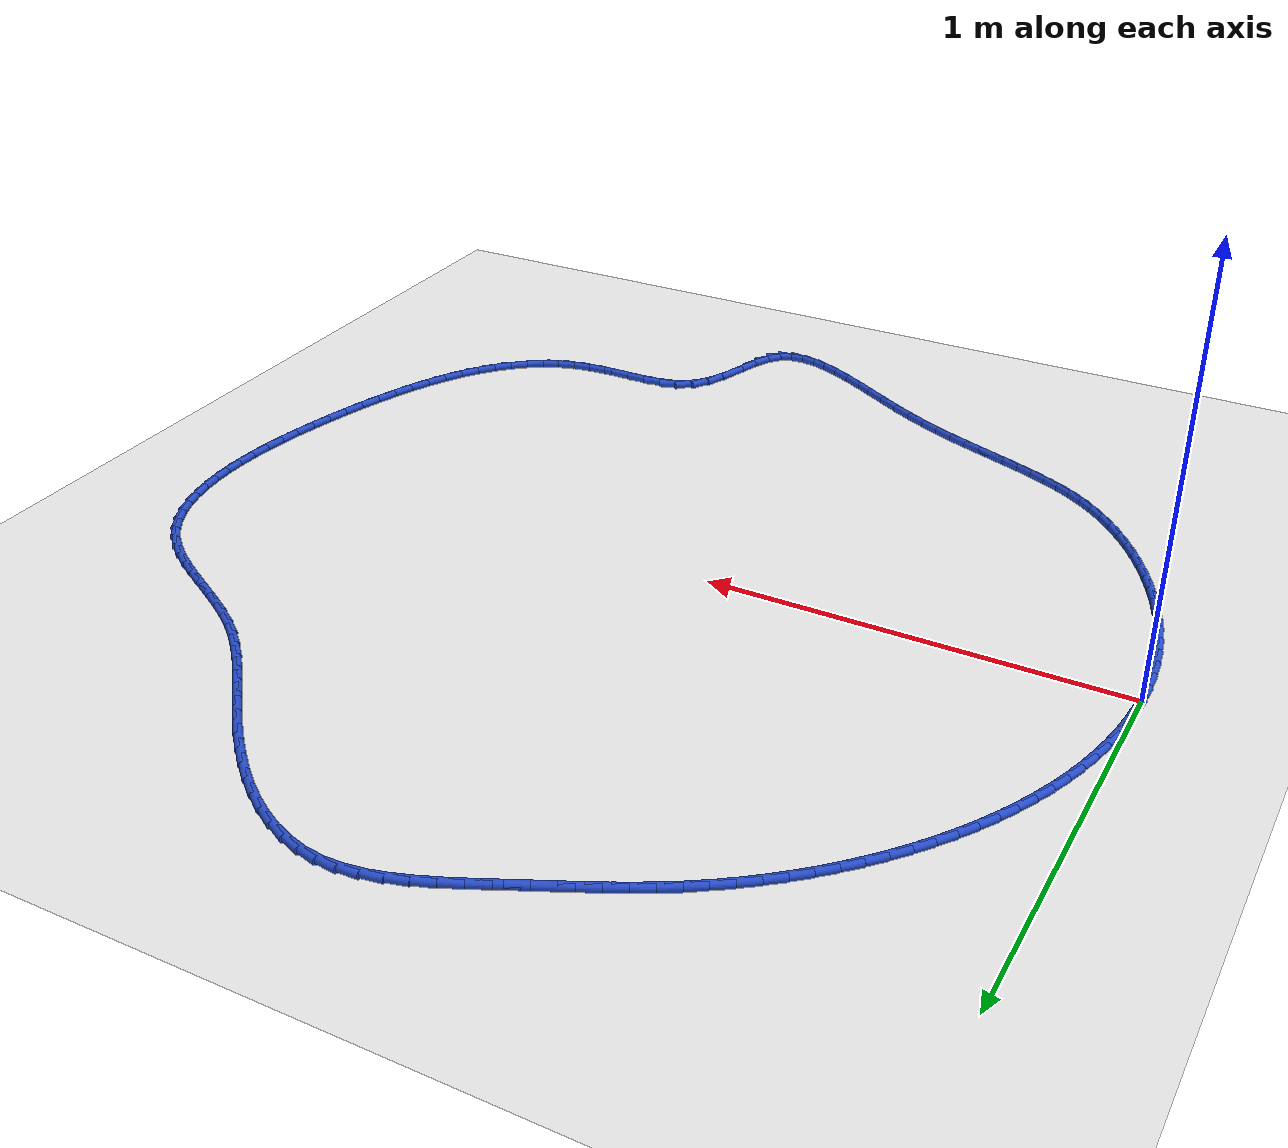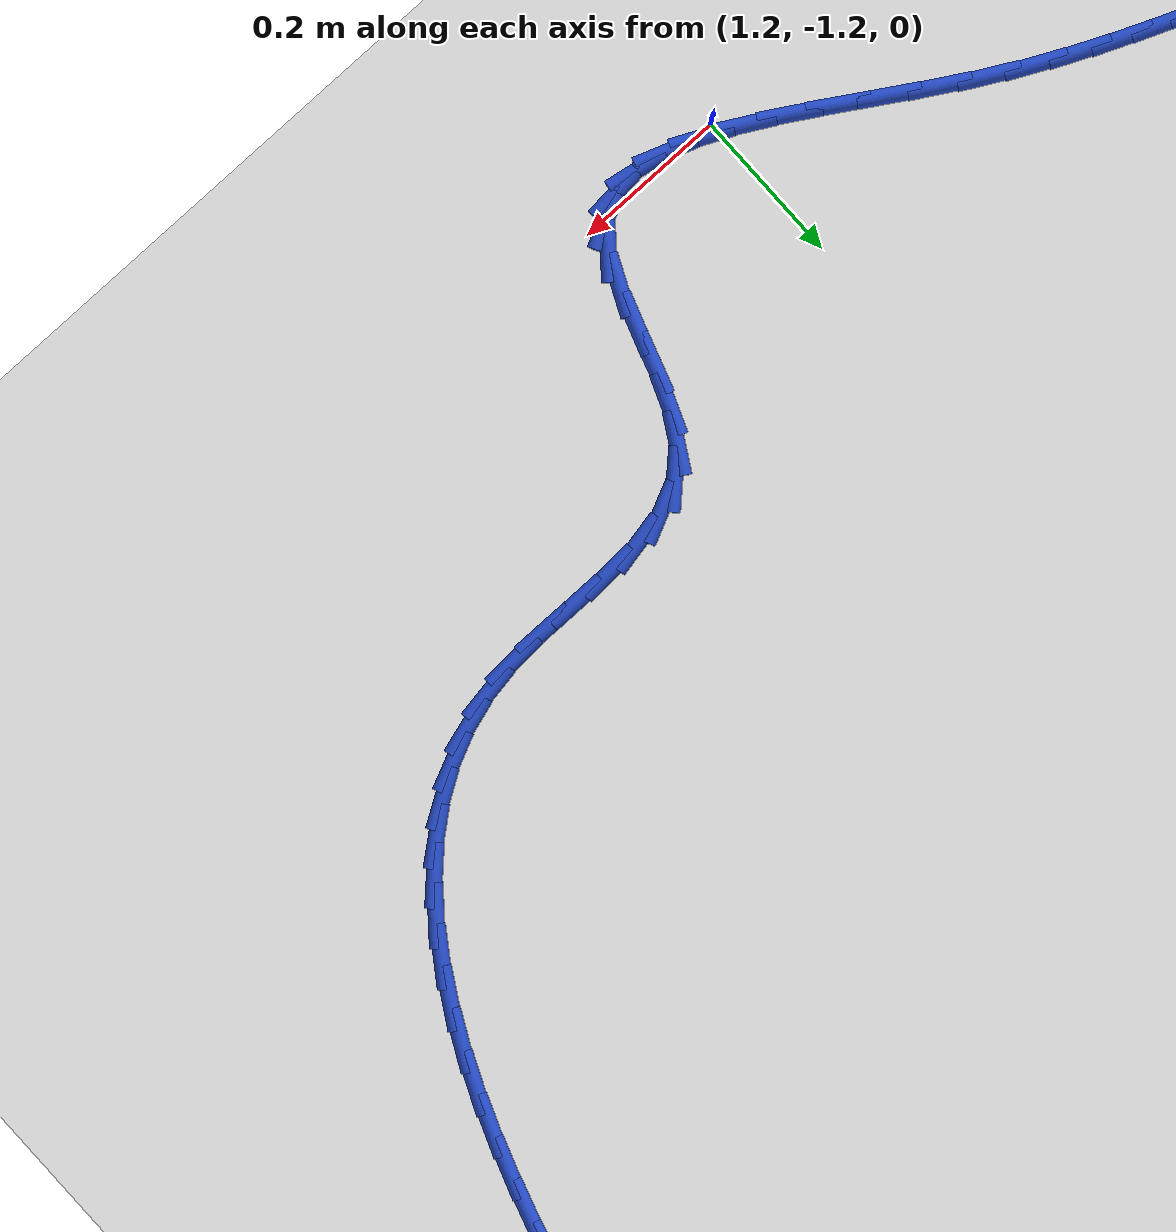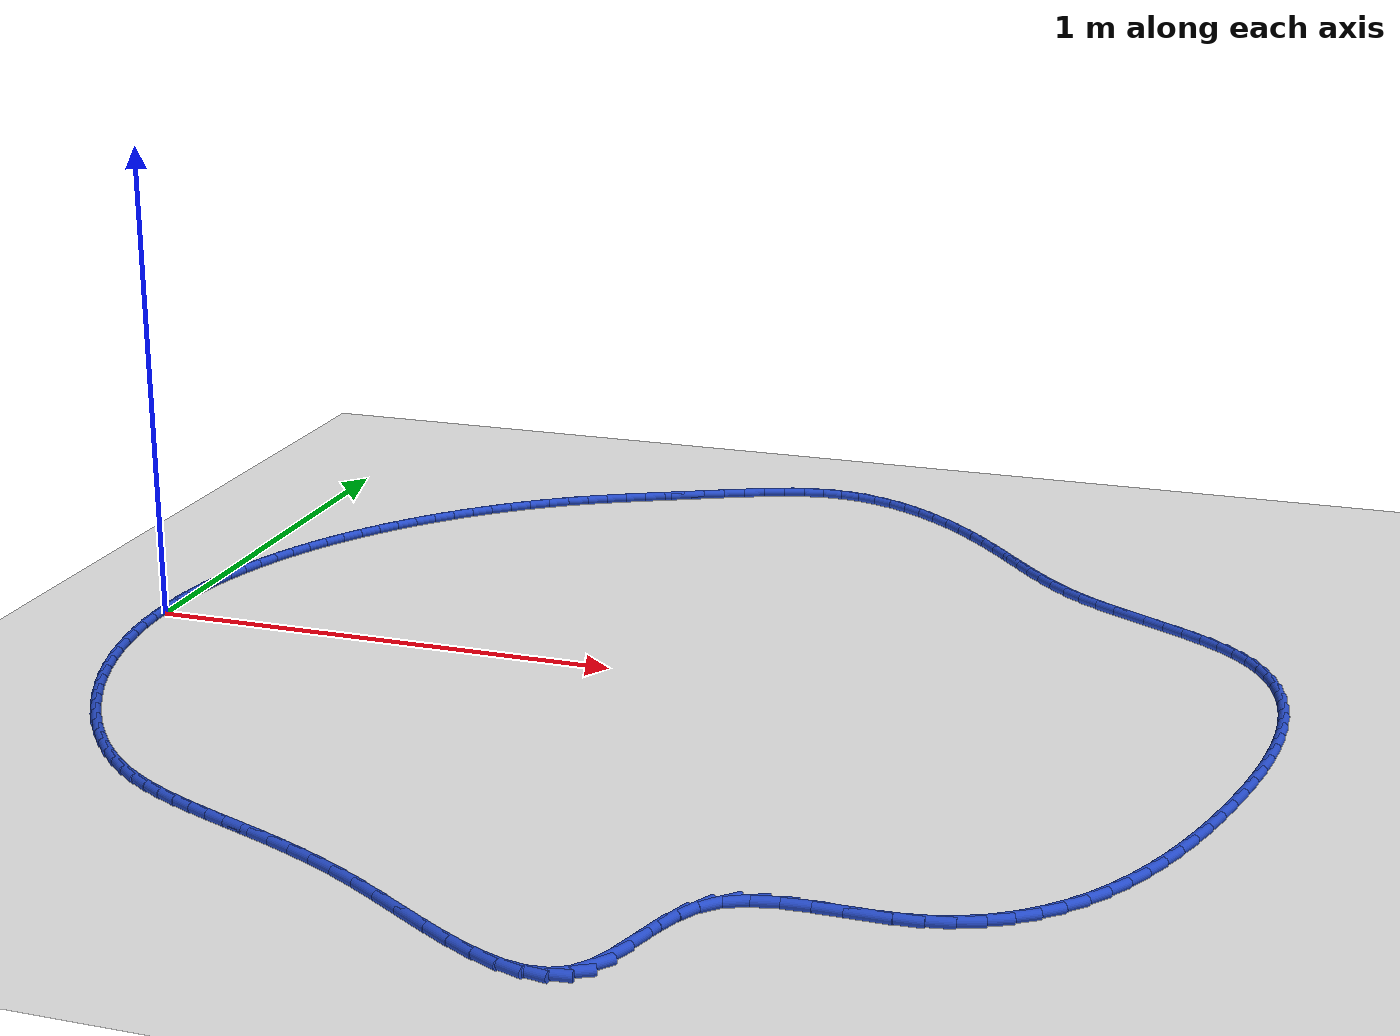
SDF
<sdf version="1.6">
 <world name="default">
  <light name="sun" type="directional">
   <pose>0 0 10 0 -0 0</pose>
   <diffuse>0.8 0.8 0.8 1</diffuse>
   <specular>0.2 0.2 0.2 1</specular>
   <attenuation>
    <range>1000</range>
    <constant>0.9</constant>
    <linear>0.01</linear>
    <quadratic>0.001</quadratic>
   </attenuation>
   <direction>-0.5 0.1 -0.9</direction>
  </light>
  <model name="ground_plane">
   <static>1</static>
   <link name="link">
    <collision name="collision">
     <geometry><plane><normal>0 0 1</normal><size>100 100</size></plane></geometry>
     <surface><friction><ode><mu>100</mu><mu2>50</mu2></ode></friction></surface>
    </collision>
    <visual name="visual">
     <cast_shadows>0</cast_shadows>
     <geometry><plane><normal>0 0 1</normal><size>100 100</size></plane></geometry>
     <material>
      <script><uri>file://media/materials/scripts/gazebo.material</uri><name>Gazebo/WhiteGlow</name></script>
     </material>
    </visual>
   </link>
  </model>
  <gravity>0 0 -9.8</gravity>
  <magnetic_field>6e-06 2.3e-05 -4.2e-05</magnetic_field>
  <atmosphere type="adiabatic"/>
  <physics name="default_physics" default="0" type="ode">
   <max_step_size>0.001</max_step_size>
   <real_time_factor>1</real_time_factor>
   <real_time_update_rate>1000</real_time_update_rate>
  </physics>
  <scene><ambient>0.4 0.4 0.4 1</ambient><background>0.7 0.7 0.7 1</background><shadows>1</shadows></scene>
  <spherical_coordinates>
   <surface_model>EARTH_WGS84</surface_model>
   <latitude_deg>0</latitude_deg>
   <longitude_deg>0</longitude_deg>
   <elevation>0</elevation>
   <heading_deg>0</heading_deg>
  </spherical_coordinates>
  <model name="line">
   <link name="link_0">
    <pose>-1.734723475976807e-17 -6.938893903907228e-17 0.01 0 1.57 1.5420917679656845</pose>
    <collision name="collision">
     <geometry><cylinder><radius>0.01</radius><length>0.08</length></cylinder></geometry>
    </collision>
    <visual name="visual">
     <material>
      <script><name>Gazebo/Blue</name><uri>file://media/materials/scripts/gazebo.material</uri></script>
     </material>
     <geometry><cylinder><radius>0.01</radius><length>0.08</length></cylinder></geometry>
    </visual>
   </link>
   <link name="link_1">
    <pose>0.0013647095893725408 0.0475302462803473 0.01 0 1.57 1.4935176895903097</pose>
    <collision name="collision">
     <geometry><cylinder><radius>0.01</radius><length>0.08</length></cylinder></geometry>
    </collision>
    <visual name="visual">
     <material>
      <script><name>Gazebo/Blue</name><uri>file://media/materials/scripts/gazebo.material</uri></script>
     </material>
     <geometry><cylinder><radius>0.01</radius><length>0.08</length></cylinder></geometry>
    </visual>
   </link>
   <link name="link_2">
    <pose>0.0050424344761275395 0.09502591900114518 0.01 0 1.57 1.4459482668344668</pose>
    <collision name="collision">
     <geometry><cylinder><radius>0.01</radius><length>0.08</length></cylinder></geometry>
    </collision>
    <visual name="visual">
     <material>
      <script><name>Gazebo/Blue</name><uri>file://media/materials/scripts/gazebo.material</uri></script>
     </material>
     <geometry><cylinder><radius>0.01</radius><length>0.08</length></cylinder></geometry>
    </visual>
   </link>
   <link name="link_3">
    <pose>0.010987295502399708 0.1423950274382091 0.01 0 1.57 1.3993050739746997</pose>
    <collision name="collision">
     <geometry><cylinder><radius>0.01</radius><length>0.08</length></cylinder></geometry>
    </collision>
    <visual name="visual">
     <material>
      <script><name>Gazebo/Blue</name><uri>file://media/materials/scripts/gazebo.material</uri></script>
     </material>
     <geometry><cylinder><radius>0.01</radius><length>0.08</length></cylinder></geometry>
    </visual>
   </link>
   <link name="link_4">
    <pose>0.01915341351032378 0.18954558086735446 0.01 0 1.57 1.353498917485196</pose>
    <collision name="collision">
     <geometry><cylinder><radius>0.01</radius><length>0.08</length></cylinder></geometry>
    </collision>
    <visual name="visual">
     <material>
      <script><name>Gazebo/Blue</name><uri>file://media/materials/scripts/gazebo.material</uri></script>
     </material>
     <geometry><cylinder><radius>0.01</radius><length>0.08</length></cylinder></geometry>
    </visual>
   </link>
   <link name="link_5">
    <pose>0.029494909342034456 0.23638558856439665 0.01 0 1.57 1.3084322120844911</pose>
    <collision name="collision">
     <geometry><cylinder><radius>0.01</radius><length>0.08</length></cylinder></geometry>
    </collision>
    <visual name="visual">
     <material>
      <script><name>Gazebo/Blue</name><uri>file://media/materials/scripts/gazebo.material</uri></script>
     </material>
     <geometry><cylinder><radius>0.01</radius><length>0.08</length></cylinder></geometry>
    </visual>
   </link>
   <link name="link_6">
    <pose>0.041965903839666495 0.28282305980515127 0.01 0 1.57 1.2640010197266225</pose>
    <collision name="collision">
     <geometry><cylinder><radius>0.01</radius><length>0.08</length></cylinder></geometry>
    </collision>
    <visual name="visual">
     <material>
      <script><name>Gazebo/Blue</name><uri>file://media/materials/scripts/gazebo.material</uri></script>
     </material>
     <geometry><cylinder><radius>0.01</radius><length>0.08</length></cylinder></geometry>
    </visual>
   </link>
   <link name="link_7">
    <pose>0.056520517845354605 0.3287660038654336 0.01 0 1.57 1.2200967701889742</pose>
    <collision name="collision">
     <geometry><cylinder><radius>0.01</radius><length>0.08</length></cylinder></geometry>
    </collision>
    <visual name="visual">
     <material>
      <script><name>Gazebo/Blue</name><uri>file://media/materials/scripts/gazebo.material</uri></script>
     </material>
     <geometry><cylinder><radius>0.01</radius><length>0.08</length></cylinder></geometry>
    </visual>
   </link>
   <link name="link_8">
    <pose>0.0731128722012335 0.37412243002105905 0.01 0 1.57 1.1766103750817722</pose>
    <collision name="collision">
     <geometry><cylinder><radius>0.01</radius><length>0.08</length></cylinder></geometry>
    </collision>
    <visual name="visual">
     <material>
      <script><name>Gazebo/Blue</name><uri>file://media/materials/scripts/gazebo.material</uri></script>
     </material>
     <geometry><cylinder><radius>0.01</radius><length>0.08</length></cylinder></geometry>
    </visual>
   </link>
   <link name="link_9">
    <pose>0.09169698191835757 0.41880043032889613 0.01 0 1.57 1.1336944703138312</pose>
    <collision name="collision">
     <geometry><cylinder><radius>0.01</radius><length>0.08</length></cylinder></geometry>
    </collision>
    <visual name="visual">
     <material>
      <script><name>Gazebo/Blue</name><uri>file://media/materials/scripts/gazebo.material</uri></script>
     </material>
     <geometry><cylinder><radius>0.01</radius><length>0.08</length></cylinder></geometry>
    </visual>
   </link>
   <link name="link_10">
    <pose>0.1122164274541733 0.4627162587518477 0.01 0 1.57 1.091731364844603</pose>
    <collision name="collision">
     <geometry><cylinder><radius>0.01</radius><length>0.08</length></cylinder></geometry>
    </collision>
    <visual name="visual">
     <material>
      <script><name>Gazebo/Blue</name><uri>file://media/materials/scripts/gazebo.material</uri></script>
     </material>
     <geometry><cylinder><radius>0.01</radius><length>0.08</length></cylinder></geometry>
    </visual>
   </link>
   <link name="link_11">
    <pose>0.1345956882542499 0.5058011100610174 0.01 0 1.57 1.0506706397227428</pose>
    <collision name="collision">
     <geometry><cylinder><radius>0.01</radius><length>0.08</length></cylinder></geometry>
    </collision>
    <visual name="visual">
     <material>
      <script><name>Gazebo/Blue</name><uri>file://media/materials/scripts/gazebo.material</uri></script>
     </material>
     <geometry><cylinder><radius>0.01</radius><length>0.08</length></cylinder></geometry>
    </visual>
   </link>
   <link name="link_12">
    <pose>0.1587572034086069 0.5479877749932688 0.01 0 1.57 1.0104036781939865</pose>
    <collision name="collision">
     <geometry><cylinder><radius>0.01</radius><length>0.08</length></cylinder></geometry>
    </collision>
    <visual name="visual">
     <material>
      <script><name>Gazebo/Blue</name><uri>file://media/materials/scripts/gazebo.material</uri></script>
     </material>
     <geometry><cylinder><radius>0.01</radius><length>0.08</length></cylinder></geometry>
    </visual>
   </link>
   <link name="link_13">
    <pose>0.18462341200726387 0.5892090442854648 0.01 0 1.57 0.970816725050132</pose>
    <collision name="collision">
     <geometry><cylinder><radius>0.01</radius><length>0.08</length></cylinder></geometry>
    </collision>
    <visual name="visual">
     <material>
      <script><name>Gazebo/Blue</name><uri>file://media/materials/scripts/gazebo.material</uri></script>
     </material>
     <geometry><cylinder><radius>0.01</radius><length>0.08</length></cylinder></geometry>
    </visual>
   </link>
   <link name="link_14">
    <pose>0.21211675314024034 0.6293977086744686 0.01 0 1.57 0.93179198835614</pose>
    <collision name="collision">
     <geometry><cylinder><radius>0.01</radius><length>0.08</length></cylinder></geometry>
    </collision>
    <visual name="visual">
     <material>
      <script><name>Gazebo/Blue</name><uri>file://media/materials/scripts/gazebo.material</uri></script>
     </material>
     <geometry><cylinder><radius>0.01</radius><length>0.08</length></cylinder></geometry>
    </visual>
   </link>
   <link name="link_15">
    <pose>0.24115966589755575 0.6684865588971433 0.01 0 1.57 0.8932084274522099</pose>
    <collision name="collision">
     <geometry><cylinder><radius>0.01</radius><length>0.08</length></cylinder></geometry>
    </collision>
    <visual name="visual">
     <material>
      <script><name>Gazebo/Blue</name><uri>file://media/materials/scripts/gazebo.material</uri></script>
     </material>
     <geometry><cylinder><radius>0.01</radius><length>0.08</length></cylinder></geometry>
    </visual>
   </link>
   <link name="link_16">
    <pose>0.2716745893692297 0.7064083856903522 0.01 0 1.57 0.8549422761940746</pose>
    <collision name="collision">
     <geometry><cylinder><radius>0.01</radius><length>0.08</length></cylinder></geometry>
    </collision>
    <visual name="visual">
     <material>
      <script><name>Gazebo/Blue</name><uri>file://media/materials/scripts/gazebo.material</uri></script>
     </material>
     <geometry><cylinder><radius>0.01</radius><length>0.08</length></cylinder></geometry>
    </visual>
   </link>
   <link name="link_17">
    <pose>0.3035839626452817 0.7430959797909586 0.01 0 1.57 0.8168673510389605</pose>
    <collision name="collision">
     <geometry><cylinder><radius>0.01</radius><length>0.08</length></cylinder></geometry>
    </collision>
    <visual name="visual">
     <material>
      <script><name>Gazebo/Blue</name><uri>file://media/materials/scripts/gazebo.material</uri></script>
     </material>
     <geometry><cylinder><radius>0.01</radius><length>0.08</length></cylinder></geometry>
    </visual>
   </link>
   <link name="link_18">
    <pose>0.3368102248157314 0.7784821319358257 0.01 0 1.57 0.7788551930454439</pose>
    <collision name="collision">
     <geometry><cylinder><radius>0.01</radius><length>0.08</length></cylinder></geometry>
    </collision>
    <visual name="visual">
     <material>
      <script><name>Gazebo/Blue</name><uri>file://media/materials/scripts/gazebo.material</uri></script>
     </material>
     <geometry><cylinder><radius>0.01</radius><length>0.08</length></cylinder></geometry>
    </visual>
   </link>
   <link name="link_19">
    <pose>0.37127581497059814 0.8124996328618164 0.01 0 1.57 0.7407750922744352</pose>
    <collision name="collision">
     <geometry><cylinder><radius>0.01</radius><length>0.08</length></cylinder></geometry>
    </collision>
    <visual name="visual">
     <material>
      <script><name>Gazebo/Blue</name><uri>file://media/materials/scripts/gazebo.material</uri></script>
     </material>
     <geometry><cylinder><radius>0.01</radius><length>0.08</length></cylinder></geometry>
    </visual>
   </link>
   <link name="link_20">
    <pose>0.40690317219990163 0.8450812733057942 0.01 0 1.57 0.7024940433238107</pose>
    <collision name="collision">
     <geometry><cylinder><radius>0.01</radius><length>0.08</length></cylinder></geometry>
    </collision>
    <visual name="visual">
     <material>
      <script><name>Gazebo/Blue</name><uri>file://media/materials/scripts/gazebo.material</uri></script>
     </material>
     <geometry><cylinder><radius>0.01</radius><length>0.08</length></cylinder></geometry>
    </visual>
   </link>
   <link name="link_21">
    <pose>0.4436147355936613 0.8761598440046221 0.01 0 1.57 0.6638766824531006</pose>
    <collision name="collision">
     <geometry><cylinder><radius>0.01</radius><length>0.08</length></cylinder></geometry>
    </collision>
    <visual name="visual">
     <material>
      <script><name>Gazebo/Blue</name><uri>file://media/materials/scripts/gazebo.material</uri></script>
     </material>
     <geometry><cylinder><radius>0.01</radius><length>0.08</length></cylinder></geometry>
    </visual>
   </link>
   <link name="link_22">
    <pose>0.48133294424189677 0.9056681356951632 0.01 0 1.57 0.6247852604363164</pose>
    <collision name="collision">
     <geometry><cylinder><radius>0.01</radius><length>0.08</length></cylinder></geometry>
    </collision>
    <visual name="visual">
     <material>
      <script><name>Gazebo/Blue</name><uri>file://media/materials/scripts/gazebo.material</uri></script>
     </material>
     <geometry><cylinder><radius>0.01</radius><length>0.08</length></cylinder></geometry>
    </visual>
   </link>
   <link name="link_23">
    <pose>0.5199802372346274 0.933538939114281 0.01 0 1.57 0.5850797112424139</pose>
    <collision name="collision">
     <geometry><cylinder><radius>0.01</radius><length>0.08</length></cylinder></geometry>
    </collision>
    <visual name="visual">
     <material>
      <script><name>Gazebo/Blue</name><uri>file://media/materials/scripts/gazebo.material</uri></script>
     </material>
     <geometry><cylinder><radius>0.01</radius><length>0.08</length></cylinder></geometry>
    </visual>
   </link>
   <link name="link_24">
    <pose>0.559479053661873 0.9597050449988384 0.01 0 1.57 0.5456485657736976</pose>
    <collision name="collision">
     <geometry><cylinder><radius>0.01</radius><length>0.08</length></cylinder></geometry>
    </collision>
    <visual name="visual">
     <material>
      <script><name>Gazebo/Blue</name><uri>file://media/materials/scripts/gazebo.material</uri></script>
     </material>
     <geometry><cylinder><radius>0.01</radius><length>0.08</length></cylinder></geometry>
    </visual>
   </link>
   <link name="link_25">
    <pose>0.5997583481529367 0.984159973234796 0.01 0 1.57 0.511471368178422</pose>
    <collision name="collision">
     <geometry><cylinder><radius>0.01</radius><length>0.08</length></cylinder></geometry>
    </collision>
    <visual name="visual">
     <material>
      <script><name>Gazebo/Blue</name><uri>file://media/materials/scripts/gazebo.material</uri></script>
     </material>
     <geometry><cylinder><radius>0.01</radius><length>0.08</length></cylinder></geometry>
    </visual>
   </link>
   <link name="link_26">
    <pose>0.640777828214574 1.007183880930092 0.01 0 1.57 0.4843877825300081</pose>
    <collision name="collision">
     <geometry><cylinder><radius>0.01</radius><length>0.08</length></cylinder></geometry>
    </collision>
    <visual name="visual">
     <material>
      <script><name>Gazebo/Blue</name><uri>file://media/materials/scripts/gazebo.material</uri></script>
     </material>
     <geometry><cylinder><radius>0.01</radius><length>0.08</length></cylinder></geometry>
    </visual>
   </link>
   <link name="link_27">
    <pose>0.6825062659357573 1.029141413113151 0.01 0 1.57 0.464641862648612</pose>
    <collision name="collision">
     <geometry><cylinder><radius>0.01</radius><length>0.08</length></cylinder></geometry>
    </collision>
    <visual name="visual">
     <material>
      <script><name>Gazebo/Blue</name><uri>file://media/materials/scripts/gazebo.material</uri></script>
     </material>
     <geometry><cylinder><radius>0.01</radius><length>0.08</length></cylinder></geometry>
    </visual>
   </link>
   <link name="link_28">
    <pose>0.7249124346951709 1.0503972268333757 0.01 0 1.57 0.4522939385339467</pose>
    <collision name="collision">
     <geometry><cylinder><radius>0.01</radius><length>0.08</length></cylinder></geometry>
    </collision>
    <visual name="visual">
     <material>
      <script><name>Gazebo/Blue</name><uri>file://media/materials/scripts/gazebo.material</uri></script>
     </material>
     <geometry><cylinder><radius>0.01</radius><length>0.08</length></cylinder></geometry>
    </visual>
   </link>
   <link name="link_29">
    <pose>0.7679651078715 1.0713159791401672 0.01 0 1.57 0.44725437687629693</pose>
    <collision name="collision">
     <geometry><cylinder><radius>0.01</radius><length>0.08</length></cylinder></geometry>
    </collision>
    <visual name="visual">
     <material>
      <script><name>Gazebo/Blue</name><uri>file://media/materials/scripts/gazebo.material</uri></script>
     </material>
     <geometry><cylinder><radius>0.01</radius><length>0.08</length></cylinder></geometry>
    </visual>
   </link>
   <link name="link_30">
    <pose>0.8116330588434293 1.0922623270829284 0.01 0 1.57 0.44919323965143126</pose>
    <collision name="collision">
     <geometry><cylinder><radius>0.01</radius><length>0.08</length></cylinder></geometry>
    </collision>
    <visual name="visual">
     <material>
      <script><name>Gazebo/Blue</name><uri>file://media/materials/scripts/gazebo.material</uri></script>
     </material>
     <geometry><cylinder><radius>0.01</radius><length>0.08</length></cylinder></geometry>
    </visual>
   </link>
   <link name="link_31">
    <pose>0.8558846248289208 1.113594256516092 0.01 0 1.57 0.44895959401500124</pose>
    <collision name="collision">
     <geometry><cylinder><radius>0.01</radius><length>0.08</length></cylinder></geometry>
    </collision>
    <visual name="visual">
     <material>
      <script><name>Gazebo/Blue</name><uri>file://media/materials/scripts/gazebo.material</uri></script>
     </material>
     <geometry><cylinder><radius>0.01</radius><length>0.08</length></cylinder></geometry>
    </visual>
   </link>
   <link name="link_32">
    <pose>0.9006550386156962 1.1351634121748793 0.01 0 1.57 0.43164333140419925</pose>
    <collision name="collision">
     <geometry><cylinder><radius>0.01</radius><length>0.08</length></cylinder></geometry>
    </collision>
    <visual name="visual">
     <material>
      <script><name>Gazebo/Blue</name><uri>file://media/materials/scripts/gazebo.material</uri></script>
     </material>
     <geometry><cylinder><radius>0.01</radius><length>0.08</length></cylinder></geometry>
    </visual>
   </link>
   <link name="link_33">
    <pose>0.9458237781266914 1.155968653217696 0.01 0 1.57 0.39524928359702854</pose>
    <collision name="collision">
     <geometry><cylinder><radius>0.01</radius><length>0.08</length></cylinder></geometry>
    </collision>
    <visual name="visual">
     <material>
      <script><name>Gazebo/Blue</name><uri>file://media/materials/scripts/gazebo.material</uri></script>
     </material>
     <geometry><cylinder><radius>0.01</radius><length>0.08</length></cylinder></geometry>
    </visual>
   </link>
   <link name="link_34">
    <pose>0.9912649654547276 1.1749269199481416 0.01 0 1.57 0.3380912448658627</pose>
    <collision name="collision">
     <geometry><cylinder><radius>0.01</radius><length>0.08</length></cylinder></geometry>
    </collision>
    <visual name="visual">
     <material>
      <script><name>Gazebo/Blue</name><uri>file://media/materials/scripts/gazebo.material</uri></script>
     </material>
     <geometry><cylinder><radius>0.01</radius><length>0.08</length></cylinder></geometry>
    </visual>
   </link>
   <link name="link_35">
    <pose>1.0368527226926265 1.1909551526698154 0.01 0 1.57 0.2575885385305117</pose>
    <collision name="collision">
     <geometry><cylinder><radius>0.01</radius><length>0.08</length></cylinder></geometry>
    </collision>
    <visual name="visual">
     <material>
      <script><name>Gazebo/Blue</name><uri>file://media/materials/scripts/gazebo.material</uri></script>
     </material>
     <geometry><cylinder><radius>0.01</radius><length>0.08</length></cylinder></geometry>
    </visual>
   </link>
   <link name="link_36">
    <pose>1.0824611719332091 1.2029702916863176 0.01 0 1.57 0.1508988379513325</pose>
    <collision name="collision">
     <geometry><cylinder><radius>0.01</radius><length>0.08</length></cylinder></geometry>
    </collision>
    <visual name="visual">
     <material>
      <script><name>Gazebo/Blue</name><uri>file://media/materials/scripts/gazebo.material</uri></script>
     </material>
     <geometry><cylinder><radius>0.01</radius><length>0.08</length></cylinder></geometry>
    </visual>
   </link>
   <link name="link_37">
    <pose>1.127964435269297 1.2098892773012475 0.01 0 1.57 0.01643444134484584</pose>
    <collision name="collision">
     <geometry><cylinder><radius>0.01</radius><length>0.08</length></cylinder></geometry>
    </collision>
    <visual name="visual">
     <material>
      <script><name>Gazebo/Blue</name><uri>file://media/materials/scripts/gazebo.material</uri></script>
     </material>
     <geometry><cylinder><radius>0.01</radius><length>0.08</length></cylinder></geometry>
    </visual>
   </link>
   <link name="link_38">
    <pose>1.1732365240993912 1.2106333657813904 0.01 0 1.57 -0.1320077367489948</pose>
    <collision name="collision">
     <geometry><cylinder><radius>0.01</radius><length>0.08</length></cylinder></geometry>
    </collision>
    <visual name="visual">
     <material>
      <script><name>Gazebo/Blue</name><uri>file://media/materials/scripts/gazebo.material</uri></script>
     </material>
     <geometry><cylinder><radius>0.01</radius><length>0.08</length></cylinder></geometry>
    </visual>
   </link>
   <link name="link_39">
    <pose>1.218137404719517 1.204671430876612 0.01 0 1.57 -0.26673175967133944</pose>
    <collision name="collision">
     <geometry><cylinder><radius>0.01</radius><length>0.08</length></cylinder></geometry>
    </collision>
    <visual name="visual">
     <material>
      <script><name>Gazebo/Blue</name><uri>file://media/materials/scripts/gazebo.material</uri></script>
     </material>
     <geometry><cylinder><radius>0.01</radius><length>0.08</length></cylinder></geometry>
    </visual>
   </link>
   <link name="link_40">
    <pose>1.262499408350668 1.1925498358219668 0.01 0 1.57 -0.3834303766878469</pose>
    <collision name="collision">
     <geometry><cylinder><radius>0.01</radius><length>0.08</length></cylinder></geometry>
    </collision>
    <visual name="visual">
     <material>
      <script><name>Gazebo/Blue</name><uri>file://media/materials/scripts/gazebo.material</uri></script>
     </material>
     <geometry><cylinder><radius>0.01</radius><length>0.08</length></cylinder></geometry>
    </visual>
   </link>
   <link name="link_41">
    <pose>1.3061516406656701 1.1749407077315244 0.01 0 1.57 -0.48288711895890274</pose>
    <collision name="collision">
     <geometry><cylinder><radius>0.01</radius><length>0.08</length></cylinder></geometry>
    </collision>
    <visual name="visual">
     <material>
      <script><name>Gazebo/Blue</name><uri>file://media/materials/scripts/gazebo.material</uri></script>
     </material>
     <geometry><cylinder><radius>0.01</radius><length>0.08</length></cylinder></geometry>
    </visual>
   </link>
   <link name="link_42">
    <pose>1.3489232073373485 1.1525161737193543 0.01 0 1.57 -0.567048485277732</pose>
    <collision name="collision">
     <geometry><cylinder><radius>0.01</radius><length>0.08</length></cylinder></geometry>
    </collision>
    <visual name="visual">
     <material>
      <script><name>Gazebo/Blue</name><uri>file://media/materials/scripts/gazebo.material</uri></script>
     </material>
     <geometry><cylinder><radius>0.01</radius><length>0.08</length></cylinder></geometry>
    </visual>
   </link>
   <link name="link_43">
    <pose>1.3906432140385299 1.1259483608995267 0.01 0 1.57 -0.638198653560492</pose>
    <collision name="collision">
     <geometry><cylinder><radius>0.01</radius><length>0.08</length></cylinder></geometry>
    </collision>
    <visual name="visual">
     <material>
      <script><name>Gazebo/Blue</name><uri>file://media/materials/scripts/gazebo.material</uri></script>
     </material>
     <geometry><cylinder><radius>0.01</radius><length>0.08</length></cylinder></geometry>
    </visual>
   </link>
   <link name="link_44">
    <pose>1.4311407664420395 1.0959093963861104 0.01 0 1.57 -0.6985167395385447</pose>
    <collision name="collision">
     <geometry><cylinder><radius>0.01</radius><length>0.08</length></cylinder></geometry>
    </collision>
    <visual name="visual">
     <material>
      <script><name>Gazebo/Blue</name><uri>file://media/materials/scripts/gazebo.material</uri></script>
     </material>
     <geometry><cylinder><radius>0.01</radius><length>0.08</length></cylinder></geometry>
    </visual>
   </link>
   <link name="link_45">
    <pose>1.4702449702207046 1.0630714072931753 0.01 0 1.57 -0.7498971939405806</pose>
    <collision name="collision">
     <geometry><cylinder><radius>0.01</radius><length>0.08</length></cylinder></geometry>
    </collision>
    <visual name="visual">
     <material>
      <script><name>Gazebo/Blue</name><uri>file://media/materials/scripts/gazebo.material</uri></script>
     </material>
     <geometry><cylinder><radius>0.01</radius><length>0.08</length></cylinder></geometry>
    </visual>
   </link>
   <link name="link_46">
    <pose>1.50778493104735 1.0281065207347913 0.01 0 1.57 -0.7939107689178965</pose>
    <collision name="collision">
     <geometry><cylinder><radius>0.01</radius><length>0.08</length></cylinder></geometry>
    </collision>
    <visual name="visual">
     <material>
      <script><name>Gazebo/Blue</name><uri>file://media/materials/scripts/gazebo.material</uri></script>
     </material>
     <geometry><cylinder><radius>0.01</radius><length>0.08</length></cylinder></geometry>
    </visual>
   </link>
   <link name="link_47">
    <pose>1.5435897545948023 0.9916868638250278 0.01 0 1.57 -0.8317364242147484</pose>
    <collision name="collision">
     <geometry><cylinder><radius>0.01</radius><length>0.08</length></cylinder></geometry>
    </collision>
    <visual name="visual">
     <material>
      <script><name>Gazebo/Blue</name><uri>file://media/materials/scripts/gazebo.material</uri></script>
     </material>
     <geometry><cylinder><radius>0.01</radius><length>0.08</length></cylinder></geometry>
    </visual>
   </link>
   <link name="link_48">
    <pose>1.5774992788975772 0.9544795481267682 0.01 0 1.57 -0.8612995934906535</pose>
    <collision name="collision">
     <geometry><cylinder><radius>0.01</radius><length>0.08</length></cylinder></geometry>
    </collision>
    <visual name="visual">
     <material>
      <script><name>Gazebo/Blue</name><uri>file://media/materials/scripts/gazebo.material</uri></script>
     </material>
     <geometry><cylinder><radius>0.01</radius><length>0.08</length></cylinder></geometry>
    </visual>
   </link>
   <link name="link_49">
    <pose>1.6096834674717633 0.9169974077662258 0.01 0 1.57 -0.8787972510236451</pose>
    <collision name="collision">
     <geometry><cylinder><radius>0.01</radius><length>0.08</length></cylinder></geometry>
    </collision>
    <visual name="visual">
     <material>
      <script><name>Gazebo/Blue</name><uri>file://media/materials/scripts/gazebo.material</uri></script>
     </material>
     <geometry><cylinder><radius>0.01</radius><length>0.08</length></cylinder></geometry>
    </visual>
   </link>
   <link name="link_50">
    <pose>1.640696612459307 0.8795736686947088 0.01 0 1.57 -0.8832782447908238</pose>
    <collision name="collision">
     <geometry><cylinder><radius>0.01</radius><length>0.08</length></cylinder></geometry>
    </collision>
    <visual name="visual">
     <material>
      <script><name>Gazebo/Blue</name><uri>file://media/materials/scripts/gazebo.material</uri></script>
     </material>
     <geometry><cylinder><radius>0.01</radius><length>0.08</length></cylinder></geometry>
    </visual>
   </link>
   <link name="link_51">
    <pose>1.6711146575934945 0.8425314384322062 0.01 0 1.57 -0.8741520365505587</pose>
    <collision name="collision">
     <geometry><cylinder><radius>0.01</radius><length>0.08</length></cylinder></geometry>
    </collision>
    <visual name="visual">
     <material>
      <script><name>Gazebo/Blue</name><uri>file://media/materials/scripts/gazebo.material</uri></script>
     </material>
     <geometry><cylinder><radius>0.01</radius><length>0.08</length></cylinder></geometry>
    </visual>
   </link>
   <link name="link_52">
    <pose>1.7015135466076117 0.8061938244987067 0.01 0 1.57 -0.8510123768698182</pose>
    <collision name="collision">
     <geometry><cylinder><radius>0.01</radius><length>0.08</length></cylinder></geometry>
    </collision>
    <visual name="visual">
     <material>
      <script><name>Gazebo/Blue</name><uri>file://media/materials/scripts/gazebo.material</uri></script>
     </material>
     <geometry><cylinder><radius>0.01</radius><length>0.08</length></cylinder></geometry>
    </visual>
   </link>
   <link name="link_53">
    <pose>1.7324692232349455 0.7708839344141994 0.01 0 1.57 -0.8137134171846704</pose>
    <collision name="collision">
     <geometry><cylinder><radius>0.01</radius><length>0.08</length></cylinder></geometry>
    </collision>
    <visual name="visual">
     <material>
      <script><name>Gazebo/Blue</name><uri>file://media/materials/scripts/gazebo.material</uri></script>
     </material>
     <geometry><cylinder><radius>0.01</radius><length>0.08</length></cylinder></geometry>
    </visual>
   </link>
   <link name="link_54">
    <pose>1.7645576312087823 0.7369248756986729 0.01 0 1.57 -0.7625221179810815</pose>
    <collision name="collision">
     <geometry><cylinder><radius>0.01</radius><length>0.08</length></cylinder></geometry>
    </collision>
    <visual name="visual">
     <material>
      <script><name>Gazebo/Blue</name><uri>file://media/materials/scripts/gazebo.material</uri></script>
     </material>
     <geometry><cylinder><radius>0.01</radius><length>0.08</length></cylinder></geometry>
    </visual>
   </link>
   <link name="link_55">
    <pose>1.7983547142624072 0.7046397558721166 0.01 0 1.57 -0.6983257070535217</pose>
    <collision name="collision">
     <geometry><cylinder><radius>0.01</radius><length>0.08</length></cylinder></geometry>
    </collision>
    <visual name="visual">
     <material>
      <script><name>Gazebo/Blue</name><uri>file://media/materials/scripts/gazebo.material</uri></script>
     </material>
     <geometry><cylinder><radius>0.01</radius><length>0.08</length></cylinder></geometry>
    </visual>
   </link>
   <link name="link_56">
    <pose>1.8344364161291082 0.6743516824545194 0.01 0 1.57 -0.6270810724023469</pose>
    <collision name="collision">
     <geometry><cylinder><radius>0.01</radius><length>0.08</length></cylinder></geometry>
    </collision>
    <visual name="visual">
     <material>
      <script><name>Gazebo/Blue</name><uri>file://media/materials/scripts/gazebo.material</uri></script>
     </material>
     <geometry><cylinder><radius>0.01</radius><length>0.08</length></cylinder></geometry>
    </visual>
   </link>
   <link name="link_57">
    <pose>1.87319657506179 0.6462639954030939 0.01 0 1.57 -0.5711431461572496</pose>
    <collision name="collision">
     <geometry><cylinder><radius>0.01</radius><length>0.08</length></cylinder></geometry>
    </collision>
    <visual name="visual">
     <material>
      <script><name>Gazebo/Blue</name><uri>file://media/materials/scripts/gazebo.material</uri></script>
     </material>
     <geometry><cylinder><radius>0.01</radius><length>0.08</length></cylinder></geometry>
    </visual>
   </link>
   <link name="link_58">
    <pose>1.914108567910837 0.6199746634441664 0.01 0 1.57 -0.5358050058602176</pose>
    <collision name="collision">
     <geometry><cylinder><radius>0.01</radius><length>0.08</length></cylinder></geometry>
    </collision>
    <visual name="visual">
     <material>
      <script><name>Gazebo/Blue</name><uri>file://media/materials/scripts/gazebo.material</uri></script>
     </material>
     <geometry><cylinder><radius>0.01</radius><length>0.08</length></cylinder></geometry>
    </visual>
   </link>
   <link name="link_59">
    <pose>1.9563556236836654 0.5948908301848832 0.01 0 1.57 -0.5197449529511883</pose>
    <collision name="collision">
     <geometry><cylinder><radius>0.01</radius><length>0.08</length></cylinder></geometry>
    </collision>
    <visual name="visual">
     <material>
      <script><name>Gazebo/Blue</name><uri>file://media/materials/scripts/gazebo.material</uri></script>
     </material>
     <geometry><cylinder><radius>0.01</radius><length>0.08</length></cylinder></geometry>
    </visual>
   </link>
   <link name="link_60">
    <pose>1.9991208623780035 0.5704195675386408 0.01 0 1.57 -0.5224244251708188</pose>
    <collision name="collision">
     <geometry><cylinder><radius>0.01</radius><length>0.08</length></cylinder></geometry>
    </collision>
    <visual name="visual">
     <material>
      <script><name>Gazebo/Blue</name><uri>file://media/materials/scripts/gazebo.material</uri></script>
     </material>
     <geometry><cylinder><radius>0.01</radius><length>0.08</length></cylinder></geometry>
    </visual>
   </link>
   <link name="link_61">
    <pose>2.041587403991579 0.5459679474188357 0.01 0 1.57 -0.5442219038253484</pose>
    <collision name="collision">
     <geometry><cylinder><radius>0.01</radius><length>0.08</length></cylinder></geometry>
    </collision>
    <visual name="visual">
     <material>
      <script><name>Gazebo/Blue</name><uri>file://media/materials/scripts/gazebo.material</uri></script>
     </material>
     <geometry><cylinder><radius>0.01</radius><length>0.08</length></cylinder></geometry>
    </visual>
   </link>
   <link name="link_62">
    <pose>2.0829383685221208 0.5209430417388642 0.01 0 1.57 -0.5864574783718789</pose>
    <collision name="collision">
     <geometry><cylinder><radius>0.01</radius><length>0.08</length></cylinder></geometry>
    </collision>
    <visual name="visual">
     <material>
      <script><name>Gazebo/Blue</name><uri>file://media/materials/scripts/gazebo.material</uri></script>
     </material>
     <geometry><cylinder><radius>0.01</radius><length>0.08</length></cylinder></geometry>
    </visual>
   </link>
   <link name="link_63">
    <pose>2.122356875967355 0.4947519224121236 0.01 0 1.57 -0.6512810797571525</pose>
    <collision name="collision">
     <geometry><cylinder><radius>0.01</radius><length>0.08</length></cylinder></geometry>
    </collision>
    <visual name="visual">
     <material>
      <script><name>Gazebo/Blue</name><uri>file://media/materials/scripts/gazebo.material</uri></script>
     </material>
     <geometry><cylinder><radius>0.01</radius><length>0.08</length></cylinder></geometry>
    </visual>
   </link>
   <link name="link_64">
    <pose>2.1590260463250104 0.4668016613520102 0.01 0 1.57 -0.7412566819356411</pose>
    <collision name="collision">
     <geometry><cylinder><radius>0.01</radius><length>0.08</length></cylinder></geometry>
    </collision>
    <visual name="visual">
     <material>
      <script><name>Gazebo/Blue</name><uri>file://media/materials/scripts/gazebo.material</uri></script>
     </material>
     <geometry><cylinder><radius>0.01</radius><length>0.08</length></cylinder></geometry>
    </visual>
   </link>
   <link name="link_65">
    <pose>2.192128999592815 0.43649933047192035 0.01 0 1.57 -0.8556403793179593</pose>
    <collision name="collision">
     <geometry><cylinder><radius>0.01</radius><length>0.08</length></cylinder></geometry>
    </collision>
    <visual name="visual">
     <material>
      <script><name>Gazebo/Blue</name><uri>file://media/materials/scripts/gazebo.material</uri></script>
     </material>
     <geometry><cylinder><radius>0.01</radius><length>0.08</length></cylinder></geometry>
    </visual>
   </link>
   <link name="link_66">
    <pose>2.22094229724467 0.4033246872152758 0.01 0 1.57 -0.9748060117624547</pose>
    <collision name="collision">
     <geometry><cylinder><radius>0.01</radius><length>0.08</length></cylinder></geometry>
    </collision>
    <visual name="visual">
     <material>
      <script><name>Gazebo/Blue</name><uri>file://media/materials/scripts/gazebo.material</uri></script>
     </material>
     <geometry><cylinder><radius>0.01</radius><length>0.08</length></cylinder></geometry>
    </visual>
   </link>
   <link name="link_67">
    <pose>2.245398496155504 0.3672677696350328 0.01 0 1.57 -1.087772105616212</pose>
    <collision name="collision">
     <geometry><cylinder><radius>0.01</radius><length>0.08</length></cylinder></geometry>
    </collision>
    <visual name="visual">
     <material>
      <script><name>Gazebo/Blue</name><uri>file://media/materials/scripts/gazebo.material</uri></script>
     </material>
     <geometry><cylinder><radius>0.01</radius><length>0.08</length></cylinder></geometry>
    </visual>
   </link>
   <link name="link_68">
    <pose>2.2657111603057873 0.3285372034097275 0.01 0 1.57 -1.192261541239211</pose>
    <collision name="collision">
     <geometry><cylinder><radius>0.01</radius><length>0.08</length></cylinder></geometry>
    </collision>
    <visual name="visual">
     <material>
      <script><name>Gazebo/Blue</name><uri>file://media/materials/scripts/gazebo.material</uri></script>
     </material>
     <geometry><cylinder><radius>0.01</radius><length>0.08</length></cylinder></geometry>
    </visual>
   </link>
   <link name="link_69">
    <pose>2.2820949230537404 0.2873424460571554 0.01 0 1.57 -1.2870716525226455</pose>
    <collision name="collision">
     <geometry><cylinder><radius>0.01</radius><length>0.08</length></cylinder></geometry>
    </collision>
    <visual name="visual">
     <material>
      <script><name>Gazebo/Blue</name><uri>file://media/materials/scripts/gazebo.material</uri></script>
     </material>
     <geometry><cylinder><radius>0.01</radius><length>0.08</length></cylinder></geometry>
    </visual>
   </link>
   <link name="link_70">
    <pose>2.2947644177575834 0.243892955095112 0.01 0 1.57 -1.371902595737185</pose>
    <collision name="collision">
     <geometry><cylinder><radius>0.01</radius><length>0.08</length></cylinder></geometry>
    </collision>
    <visual name="visual">
     <material>
      <script><name>Gazebo/Blue</name><uri>file://media/materials/scripts/gazebo.material</uri></script>
     </material>
     <geometry><cylinder><radius>0.01</radius><length>0.08</length></cylinder></geometry>
    </visual>
   </link>
   <link name="link_71">
    <pose>2.3039342777755363 0.19839818804139267 0.01 0 1.57 -1.447095940128062</pose>
    <collision name="collision">
     <geometry><cylinder><radius>0.01</radius><length>0.08</length></cylinder></geometry>
    </collision>
    <visual name="visual">
     <material>
      <script><name>Gazebo/Blue</name><uri>file://media/materials/scripts/gazebo.material</uri></script>
     </material>
     <geometry><cylinder><radius>0.01</radius><length>0.08</length></cylinder></geometry>
    </visual>
   </link>
   <link name="link_72">
    <pose>2.3098191364658196 0.15106760241379374 0.01 0 1.57 -1.5133704369451932</pose>
    <collision name="collision">
     <geometry><cylinder><radius>0.01</radius><length>0.08</length></cylinder></geometry>
    </collision>
    <visual name="visual">
     <material>
      <script><name>Gazebo/Blue</name><uri>file://media/materials/scripts/gazebo.material</uri></script>
     </material>
     <geometry><cylinder><radius>0.01</radius><length>0.08</length></cylinder></geometry>
    </visual>
   </link>
   <link name="link_73">
    <pose>2.3126336271866514 0.10211065573011041 0.01 0 1.57 1.5699775710118906</pose>
    <collision name="collision">
     <geometry><cylinder><radius>0.01</radius><length>0.08</length></cylinder></geometry>
    </collision>
    <visual name="visual">
     <material>
      <script><name>Gazebo/Blue</name><uri>file://media/materials/scripts/gazebo.material</uri></script>
     </material>
     <geometry><cylinder><radius>0.01</radius><length>0.08</length></cylinder></geometry>
    </visual>
   </link>
   <link name="link_74">
    <pose>2.312592383296254 0.05173680550813844 0.01 0 1.57 1.5188408438026684</pose>
    <collision name="collision">
     <geometry><cylinder><radius>0.01</radius><length>0.08</length></cylinder></geometry>
    </collision>
    <visual name="visual">
     <material>
      <script><name>Gazebo/Blue</name><uri>file://media/materials/scripts/gazebo.material</uri></script>
     </material>
     <geometry><cylinder><radius>0.01</radius><length>0.08</length></cylinder></geometry>
    </visual>
   </link>
   <link name="link_75">
    <pose>2.3099100381528466 0.00015550926567339807 0.01 0 1.57 1.473936387391252</pose>
    <collision name="collision">
     <geometry><cylinder><radius>0.01</radius><length>0.08</length></cylinder></geometry>
    </collision>
    <visual name="visual">
     <material>
      <script><name>Gazebo/Blue</name><uri>file://media/materials/scripts/gazebo.material</uri></script>
     </material>
     <geometry><cylinder><radius>0.01</radius><length>0.08</length></cylinder></geometry>
    </visual>
   </link>
   <link name="link_76">
    <pose>2.304801225114648 -0.05242377547948941 0.01 0 1.57 1.4344736659735262</pose>
    <collision name="collision">
     <geometry><cylinder><radius>0.01</radius><length>0.08</length></cylinder></geometry>
    </collision>
    <visual name="visual">
     <material>
      <script><name>Gazebo/Blue</name><uri>file://media/materials/scripts/gazebo.material</uri></script>
     </material>
     <geometry><cylinder><radius>0.01</radius><length>0.08</length></cylinder></geometry>
    </visual>
   </link>
   <link name="link_77">
    <pose>2.29748057753988 -0.10579159120955402 0.01 0 1.57 1.3997612064832197</pose>
    <collision name="collision">
     <geometry><cylinder><radius>0.01</radius><length>0.08</length></cylinder></geometry>
    </collision>
    <visual name="visual">
     <material>
      <script><name>Gazebo/Blue</name><uri>file://media/materials/scripts/gazebo.material</uri></script>
     </material>
     <geometry><cylinder><radius>0.01</radius><length>0.08</length></cylinder></geometry>
    </visual>
   </link>
   <link name="link_78">
    <pose>2.2881627287867614 -0.15973848040672395 0.01 0 1.57 1.369206772221429</pose>
    <collision name="collision">
     <geometry><cylinder><radius>0.01</radius><length>0.08</length></cylinder></geometry>
    </collision>
    <visual name="visual">
     <material>
      <script><name>Gazebo/Blue</name><uri>file://media/materials/scripts/gazebo.material</uri></script>
     </material>
     <geometry><cylinder><radius>0.01</radius><length>0.08</length></cylinder></geometry>
    </visual>
   </link>
   <link name="link_79">
    <pose>2.2770623122135127 -0.2140549855532052 0.01 0 1.57 1.3423108415167433</pose>
    <collision name="collision">
     <geometry><cylinder><radius>0.01</radius><length>0.08</length></cylinder></geometry>
    </collision>
    <visual name="visual">
     <material>
      <script><name>Gazebo/Blue</name><uri>file://media/materials/scripts/gazebo.material</uri></script>
     </material>
     <geometry><cylinder><radius>0.01</radius><length>0.08</length></cylinder></geometry>
    </visual>
   </link>
   <link name="link_80">
    <pose>2.2643939611783526 -0.26853164913120037 0.01 0 1.57 1.3186073863454515</pose>
    <collision name="collision">
     <geometry><cylinder><radius>0.01</radius><length>0.08</length></cylinder></geometry>
    </collision>
    <visual name="visual">
     <material>
      <script><name>Gazebo/Blue</name><uri>file://media/materials/scripts/gazebo.material</uri></script>
     </material>
     <geometry><cylinder><radius>0.01</radius><length>0.08</length></cylinder></geometry>
    </visual>
   </link>
   <link name="link_81">
    <pose>2.2503697404050595 -0.32295767770993594 0.01 0 1.57 1.2950604817317486</pose>
    <collision name="collision">
     <geometry><cylinder><radius>0.01</radius><length>0.08</length></cylinder></geometry>
    </collision>
    <visual name="visual">
     <material>
      <script><name>Gazebo/Blue</name><uri>file://media/materials/scripts/gazebo.material</uri></script>
     </material>
     <geometry><cylinder><radius>0.01</radius><length>0.08</length></cylinder></geometry>
    </visual>
   </link>
   <link name="link_82">
    <pose>2.235064436088429 -0.3770508811018196 0.01 0 1.57 1.2672904556955817</pose>
    <collision name="collision">
     <geometry><cylinder><radius>0.01</radius><length>0.08</length></cylinder></geometry>
    </collision>
    <visual name="visual">
     <material>
      <script><name>Gazebo/Blue</name><uri>file://media/materials/scripts/gazebo.material</uri></script>
     </material>
     <geometry><cylinder><radius>0.01</radius><length>0.08</length></cylinder></geometry>
    </visual>
   </link>
   <link name="link_83">
    <pose>2.2183492088608707 -0.43042316614326237 0.01 0 1.57 1.2344397856122422</pose>
    <collision name="collision">
     <geometry><cylinder><radius>0.01</radius><length>0.08</length></cylinder></geometry>
    </collision>
    <visual name="visual">
     <material>
      <script><name>Gazebo/Blue</name><uri>file://media/materials/scripts/gazebo.material</uri></script>
     </material>
     <geometry><cylinder><radius>0.01</radius><length>0.08</length></cylinder></geometry>
    </visual>
   </link>
   <link name="link_84">
    <pose>2.2000787312735546 -0.4826778644365525 0.01 0 1.57 1.1958258737990637</pose>
    <collision name="collision">
     <geometry><cylinder><radius>0.01</radius><length>0.08</length></cylinder></geometry>
    </collision>
    <visual name="visual">
     <material>
      <script><name>Gazebo/Blue</name><uri>file://media/materials/scripts/gazebo.material</uri></script>
     </material>
     <geometry><cylinder><radius>0.01</radius><length>0.08</length></cylinder></geometry>
    </visual>
   </link>
   <link name="link_85">
    <pose>2.180107675877653 -0.5334183075839746 0.01 0 1.57 1.150607880453237</pose>
    <collision name="collision">
     <geometry><cylinder><radius>0.01</radius><length>0.08</length></cylinder></geometry>
    </collision>
    <visual name="visual">
     <material>
      <script><name>Gazebo/Blue</name><uri>file://media/materials/scripts/gazebo.material</uri></script>
     </material>
     <geometry><cylinder><radius>0.01</radius><length>0.08</length></cylinder></geometry>
    </visual>
   </link>
   <link name="link_86">
    <pose>2.158290715224338 -0.5822478271878169 0.01 0 1.57 1.0977827968150167</pose>
    <collision name="collision">
     <geometry><cylinder><radius>0.01</radius><length>0.08</length></cylinder></geometry>
    </collision>
    <visual name="visual">
     <material>
      <script><name>Gazebo/Blue</name><uri>file://media/materials/scripts/gazebo.material</uri></script>
     </material>
     <geometry><cylinder><radius>0.01</radius><length>0.08</length></cylinder></geometry>
    </visual>
   </link>
   <link name="link_87">
    <pose>2.1344825218647805 -0.628769754850365 0.01 0 1.57 1.0362006165089523</pose>
    <collision name="collision">
     <geometry><cylinder><radius>0.01</radius><length>0.08</length></cylinder></geometry>
    </collision>
    <visual name="visual">
     <material>
      <script><name>Gazebo/Blue</name><uri>file://media/materials/scripts/gazebo.material</uri></script>
     </material>
     <geometry><cylinder><radius>0.01</radius><length>0.08</length></cylinder></geometry>
    </visual>
   </link>
   <link name="link_88">
    <pose>2.1085377683501534 -0.6725874221739048 0.01 0 1.57 0.9646188904463368</pose>
    <collision name="collision">
     <geometry><cylinder><radius>0.01</radius><length>0.08</length></cylinder></geometry>
    </collision>
    <visual name="visual">
     <material>
      <script><name>Gazebo/Blue</name><uri>file://media/materials/scripts/gazebo.material</uri></script>
     </material>
     <geometry><cylinder><radius>0.01</radius><length>0.08</length></cylinder></geometry>
    </visual>
   </link>
   <link name="link_89">
    <pose>2.080311127231628 -0.7133041607607241 0.01 0 1.57 0.8818271363376375</pose>
    <collision name="collision">
     <geometry><cylinder><radius>0.01</radius><length>0.08</length></cylinder></geometry>
    </collision>
    <visual name="visual">
     <material>
      <script><name>Gazebo/Blue</name><uri>file://media/materials/scripts/gazebo.material</uri></script>
     </material>
     <geometry><cylinder><radius>0.01</radius><length>0.08</length></cylinder></geometry>
    </visual>
   </link>
   <link name="link_90">
    <pose>2.0496572710603753 -0.7505233022131088 0.01 0 1.57 0.7868778822481812</pose>
    <collision name="collision">
     <geometry><cylinder><radius>0.01</radius><length>0.08</length></cylinder></geometry>
    </collision>
    <visual name="visual">
     <material>
      <script><name>Gazebo/Blue</name><uri>file://media/materials/scripts/gazebo.material</uri></script>
     </material>
     <geometry><cylinder><radius>0.01</radius><length>0.08</length></cylinder></geometry>
    </visual>
   </link>
   <link name="link_91">
    <pose>2.016430872387569 -0.783848178133345 0.01 0 1.57 0.6794480292651153</pose>
    <collision name="collision">
     <geometry><cylinder><radius>0.01</radius><length>0.08</length></cylinder></geometry>
    </collision>
    <visual name="visual">
     <material>
      <script><name>Gazebo/Blue</name><uri>file://media/materials/scripts/gazebo.material</uri></script>
     </material>
     <geometry><cylinder><radius>0.01</radius><length>0.08</length></cylinder></geometry>
    </visual>
   </link>
   <link name="link_92">
    <pose>1.980486603764378 -0.8128821201237196 0.01 0 1.57 0.5602962173215207</pose>
    <collision name="collision">
     <geometry><cylinder><radius>0.01</radius><length>0.08</length></cylinder></geometry>
    </collision>
    <visual name="visual">
     <material>
      <script><name>Gazebo/Blue</name><uri>file://media/materials/scripts/gazebo.material</uri></script>
     </material>
     <geometry><cylinder><radius>0.01</radius><length>0.08</length></cylinder></geometry>
    </visual>
   </link>
   <link name="link_93">
    <pose>1.9416791377419778 -0.8372284597865194 0.01 0 1.57 0.43166587089129704</pose>
    <collision name="collision">
     <geometry><cylinder><radius>0.01</radius><length>0.08</length></cylinder></geometry>
    </collision>
    <visual name="visual">
     <material>
      <script><name>Gazebo/Blue</name><uri>file://media/materials/scripts/gazebo.material</uri></script>
     </material>
     <geometry><cylinder><radius>0.01</radius><length>0.08</length></cylinder></geometry>
    </visual>
   </link>
   <link name="link_94">
    <pose>1.8998631468715361 -0.8564905287240303 0.01 0 1.57 0.2973661381251523</pose>
    <collision name="collision">
     <geometry><cylinder><radius>0.01</radius><length>0.08</length></cylinder></geometry>
    </collision>
    <visual name="visual">
     <material>
      <script><name>Gazebo/Blue</name><uri>file://media/materials/scripts/gazebo.material</uri></script>
     </material>
     <geometry><cylinder><radius>0.01</radius><length>0.08</length></cylinder></geometry>
    </visual>
   </link>
   <link name="link_95">
    <pose>1.8548933037042274 -0.8702716585385393 0.01 0 1.57 0.16238319996205794</pose>
    <collision name="collision">
     <geometry><cylinder><radius>0.01</radius><length>0.08</length></cylinder></geometry>
    </collision>
    <visual name="visual">
     <material>
      <script><name>Gazebo/Blue</name><uri>file://media/materials/scripts/gazebo.material</uri></script>
     </material>
     <geometry><cylinder><radius>0.01</radius><length>0.08</length></cylinder></geometry>
    </visual>
   </link>
   <link name="link_96">
    <pose>1.8066265351616315 -0.8781789943594657 0.01 0 1.57 0.05005989652725407</pose>
    <collision name="collision">
     <geometry><cylinder><radius>0.01</radius><length>0.08</length></cylinder></geometry>
    </collision>
    <visual name="visual">
     <material>
      <script><name>Gazebo/Blue</name><uri>file://media/materials/scripts/gazebo.material</uri></script>
     </material>
     <geometry><cylinder><radius>0.01</radius><length>0.08</length></cylinder></geometry>
    </visual>
   </link>
   <link name="link_97">
    <pose>1.75546515692339 -0.8807422692012107 0.01 0 1.57 -0.0025486317237157128</pose>
    <collision name="collision">
     <geometry><cylinder><radius>0.01</radius><length>0.08</length></cylinder></geometry>
    </collision>
    <visual name="visual">
     <material>
      <script><name>Gazebo/Blue</name><uri>file://media/materials/scripts/gazebo.material</uri></script>
     </material>
     <geometry><cylinder><radius>0.01</radius><length>0.08</length></cylinder></geometry>
    </visual>
   </link>
   <link name="link_98">
    <pose>1.703063246729208 -0.8806087157413398 0.01 0 1.57 0.0021760531063059834</pose>
    <collision name="collision">
     <geometry><cylinder><radius>0.01</radius><length>0.08</length></cylinder></geometry>
    </collision>
    <visual name="visual">
     <material>
      <script><name>Gazebo/Blue</name><uri>file://media/materials/scripts/gazebo.material</uri></script>
     </material>
     <geometry><cylinder><radius>0.01</radius><length>0.08</length></cylinder></geometry>
    </visual>
   </link>
   <link name="link_99">
    <pose>1.651249802759668 -0.8807214647250015 0.01 0 1.57 0.06675191186062432</pose>
    <collision name="collision">
     <geometry><cylinder><radius>0.01</radius><length>0.08</length></cylinder></geometry>
    </collision>
    <visual name="visual">
     <material>
      <script><name>Gazebo/Blue</name><uri>file://media/materials/scripts/gazebo.material</uri></script>
     </material>
     <geometry><cylinder><radius>0.01</radius><length>0.08</length></cylinder></geometry>
    </visual>
   </link>
   <link name="link_100">
    <pose>1.6018538231953552 -0.8840236468973434 0.01 0 1.57 0.206002344046326</pose>
    <collision name="collision">
     <geometry><cylinder><radius>0.01</radius><length>0.08</length></cylinder></geometry>
    </collision>
    <visual name="visual">
     <material>
      <script><name>Gazebo/Blue</name><uri>file://media/materials/scripts/gazebo.material</uri></script>
     </material>
     <geometry><cylinder><radius>0.01</radius><length>0.08</length></cylinder></geometry>
    </visual>
   </link>
   <link name="link_101">
    <pose>1.5567043062168537 -0.8934583930035128 0.01 0 1.57 0.4424092823524292</pose>
    <collision name="collision">
     <geometry><cylinder><radius>0.01</radius><length>0.08</length></cylinder></geometry>
    </collision>
    <visual name="visual">
     <material>
      <script><name>Gazebo/Blue</name><uri>file://media/materials/scripts/gazebo.material</uri></script>
     </material>
     <geometry><cylinder><radius>0.01</radius><length>0.08</length></cylinder></geometry>
    </visual>
   </link>
   <link name="link_102">
    <pose>1.517630250004746 -0.9119688337886586 0.01 0 1.57 0.7711733082926068</pose>
    <collision name="collision">
     <geometry><cylinder><radius>0.01</radius><length>0.08</length></cylinder></geometry>
    </collision>
    <visual name="visual">
     <material>
      <script><name>Gazebo/Blue</name><uri>file://media/materials/scripts/gazebo.material</uri></script>
     </material>
     <geometry><cylinder><radius>0.01</radius><length>0.08</length></cylinder></geometry>
    </visual>
   </link>
   <link name="link_103">
    <pose>1.4863739861095528 -0.9423482795041932 0.01 0 1.57 1.0504179033292225</pose>
    <collision name="collision">
     <geometry><cylinder><radius>0.01</radius><length>0.08</length></cylinder></geometry>
    </collision>
    <visual name="visual">
     <material>
      <script><name>Gazebo/Blue</name><uri>file://media/materials/scripts/gazebo.material</uri></script>
     </material>
     <geometry><cylinder><radius>0.01</radius><length>0.08</length></cylinder></geometry>
    </visual>
   </link>
   <link name="link_104">
    <pose>1.4626103411475355 -0.9838159472376871 0.01 0 1.57 1.2000997598057168</pose>
    <collision name="collision">
     <geometry><cylinder><radius>0.01</radius><length>0.08</length></cylinder></geometry>
    </collision>
    <visual name="visual">
     <material>
      <script><name>Gazebo/Blue</name><uri>file://media/materials/scripts/gazebo.material</uri></script>
     </material>
     <geometry><cylinder><radius>0.01</radius><length>0.08</length></cylinder></geometry>
    </visual>
   </link>
   <link name="link_105">
    <pose>1.4439045705642541 -1.0319442410631512 0.01 0 1.57 1.2590220953606888</pose>
    <collision name="collision">
     <geometry><cylinder><radius>0.01</radius><length>0.08</length></cylinder></geometry>
    </collision>
    <visual name="visual">
     <material>
      <script><name>Gazebo/Blue</name><uri>file://media/materials/scripts/gazebo.material</uri></script>
     </material>
     <geometry><cylinder><radius>0.01</radius><length>0.08</length></cylinder></geometry>
    </visual>
   </link>
   <link name="link_106">
    <pose>1.4277268488578911 -1.0821411987411664 0.01 0 1.57 1.2436134570174953</pose>
    <collision name="collision">
     <geometry><cylinder><radius>0.01</radius><length>0.08</length></cylinder></geometry>
    </collision>
    <visual name="visual">
     <material>
      <script><name>Gazebo/Blue</name><uri>file://media/materials/scripts/gazebo.material</uri></script>
     </material>
     <geometry><cylinder><radius>0.01</radius><length>0.08</length></cylinder></geometry>
    </visual>
   </link>
   <link name="link_107">
    <pose>1.4115473505266272 -1.1298148580323155 0.01 0 1.57 1.1385544335653912</pose>
    <collision name="collision">
     <geometry><cylinder><radius>0.01</radius><length>0.08</length></cylinder></geometry>
    </collision>
    <visual name="visual">
     <material>
      <script><name>Gazebo/Blue</name><uri>file://media/materials/scripts/gazebo.material</uri></script>
     </material>
     <geometry><cylinder><radius>0.01</radius><length>0.08</length></cylinder></geometry>
    </visual>
   </link>
   <link name="link_108">
    <pose>1.3928362500686438 -1.1703732566971803 0.01 0 1.57 0.883528685970104</pose>
    <collision name="collision">
     <geometry><cylinder><radius>0.01</radius><length>0.08</length></cylinder></geometry>
    </collision>
    <visual name="visual">
     <material>
      <script><name>Gazebo/Blue</name><uri>file://media/materials/scripts/gazebo.material</uri></script>
     </material>
     <geometry><cylinder><radius>0.01</radius><length>0.08</length></cylinder></geometry>
    </visual>
   </link>
   <link name="link_109">
    <pose>1.369099725533176 -1.199293685960028 0.01 0 1.57 0.47573924008997964</pose>
    <collision name="collision">
     <geometry><cylinder><radius>0.01</radius><length>0.08</length></cylinder></geometry>
    </collision>
    <visual name="visual">
     <material>
      <script><name>Gazebo/Blue</name><uri>file://media/materials/scripts/gazebo.material</uri></script>
     </material>
     <geometry><cylinder><radius>0.01</radius><length>0.08</length></cylinder></geometry>
    </visual>
   </link>
   <link name="link_110">
    <pose>1.3392149368721225 -1.214690544847956 0.01 0 1.57 0.09526611290239778</pose>
    <collision name="collision">
     <geometry><cylinder><radius>0.01</radius><length>0.08</length></cylinder></geometry>
    </collision>
    <visual name="visual">
     <material>
      <script><name>Gazebo/Blue</name><uri>file://media/materials/scripts/gazebo.material</uri></script>
     </material>
     <geometry><cylinder><radius>0.01</radius><length>0.08</length></cylinder></geometry>
    </visual>
   </link>
   <link name="link_111">
    <pose>1.3038235950842811 -1.2180723773619735 0.01 0 1.57 -0.17025828210758084</pose>
    <collision name="collision">
     <geometry><cylinder><radius>0.01</radius><length>0.08</length></cylinder></geometry>
    </collision>
    <visual name="visual">
     <material>
      <script><name>Gazebo/Blue</name><uri>file://media/materials/scripts/gazebo.material</uri></script>
     </material>
     <geometry><cylinder><radius>0.01</radius><length>0.08</length></cylinder></geometry>
    </visual>
   </link>
   <link name="link_112">
    <pose>1.26368370344632 -1.211171417744942 0.01 0 1.57 -0.3367931946872681</pose>
    <collision name="collision">
     <geometry><cylinder><radius>0.01</radius><length>0.08</length></cylinder></geometry>
    </collision>
    <visual name="visual">
     <material>
      <script><name>Gazebo/Blue</name><uri>file://media/materials/scripts/gazebo.material</uri></script>
     </material>
     <geometry><cylinder><radius>0.01</radius><length>0.08</length></cylinder></geometry>
    </visual>
   </link>
   <link name="link_113">
    <pose>1.219553265234906 -1.1957199002397234 0.01 0 1.57 -0.43952066374098026</pose>
    <collision name="collision">
     <geometry><cylinder><radius>0.01</radius><length>0.08</length></cylinder></geometry>
    </collision>
    <visual name="visual">
     <material>
      <script><name>Gazebo/Blue</name><uri>file://media/materials/scripts/gazebo.material</uri></script>
     </material>
     <geometry><cylinder><radius>0.01</radius><length>0.08</length></cylinder></geometry>
    </visual>
   </link>
   <link name="link_114">
    <pose>1.1721902837267082 -1.1734500590891799 0.01 0 1.57 -0.5020000619410612</pose>
    <collision name="collision">
     <geometry><cylinder><radius>0.01</radius><length>0.08</length></cylinder></geometry>
    </collision>
    <visual name="visual">
     <material>
      <script><name>Gazebo/Blue</name><uri>file://media/materials/scripts/gazebo.material</uri></script>
     </material>
     <geometry><cylinder><radius>0.01</radius><length>0.08</length></cylinder></geometry>
    </visual>
   </link>
   <link name="link_115">
    <pose>1.1223527621983922 -1.1460941285361717 0.01 0 1.57 -0.537237895199799</pose>
    <collision name="collision">
     <geometry><cylinder><radius>0.01</radius><length>0.08</length></cylinder></geometry>
    </collision>
    <visual name="visual">
     <material>
      <script><name>Gazebo/Blue</name><uri>file://media/materials/scripts/gazebo.material</uri></script>
     </material>
     <geometry><cylinder><radius>0.01</radius><length>0.08</length></cylinder></geometry>
    </visual>
   </link>
   <link name="link_116">
    <pose>1.070798703926627 -1.1153843428235615 0.01 0 1.57 -0.5518754743743217</pose>
    <collision name="collision">
     <geometry><cylinder><radius>0.01</radius><length>0.08</length></cylinder></geometry>
    </collision>
    <visual name="visual">
     <material>
      <script><name>Gazebo/Blue</name><uri>file://media/materials/scripts/gazebo.material</uri></script>
     </material>
     <geometry><cylinder><radius>0.01</radius><length>0.08</length></cylinder></geometry>
    </visual>
   </link>
   <link name="link_117">
    <pose>1.0182861121880815 -1.0830529361942118 0.01 0 1.57 -0.5486491045451183</pose>
    <collision name="collision">
     <geometry><cylinder><radius>0.01</radius><length>0.08</length></cylinder></geometry>
    </collision>
    <visual name="visual">
     <material>
      <script><name>Gazebo/Blue</name><uri>file://media/materials/scripts/gazebo.material</uri></script>
     </material>
     <geometry><cylinder><radius>0.01</radius><length>0.08</length></cylinder></geometry>
    </visual>
   </link>
   <link name="link_118">
    <pose>0.9655729902594218 -1.0508321428909828 0.01 0 1.57 -0.5274135252170403</pose>
    <collision name="collision">
     <geometry><cylinder><radius>0.01</radius><length>0.08</length></cylinder></geometry>
    </collision>
    <visual name="visual">
     <material>
      <script><name>Gazebo/Blue</name><uri>file://media/materials/scripts/gazebo.material</uri></script>
     </material>
     <geometry><cylinder><radius>0.01</radius><length>0.08</length></cylinder></geometry>
    </visual>
   </link>
   <link name="link_119">
    <pose>0.9134173414161961 -1.0204541971534538 0.01 0 1.57 -0.48990386660338725</pose>
    <collision name="collision">
     <geometry><cylinder><radius>0.01</radius><length>0.08</length></cylinder></geometry>
    </collision>
    <visual name="visual">
     <material>
      <script><name>Gazebo/Blue</name><uri>file://media/materials/scripts/gazebo.material</uri></script>
     </material>
     <geometry><cylinder><radius>0.01</radius><length>0.08</length></cylinder></geometry>
    </visual>
   </link>
   <link name="link_120">
    <pose>0.8624484787636302 -0.9932743034643912 0.01 0 1.57 -0.45219903946900136</pose>
    <collision name="collision">
     <geometry><cylinder><radius>0.01</radius><length>0.08</length></cylinder></geometry>
    </collision>
    <visual name="visual">
     <material>
      <script><name>Gazebo/Blue</name><uri>file://media/materials/scripts/gazebo.material</uri></script>
     </material>
     <geometry><cylinder><radius>0.01</radius><length>0.08</length></cylinder></geometry>
    </visual>
   </link>
   <link name="link_121">
    <pose>0.8127841286339411 -0.9691488460304208 0.01 0 1.57 -0.4197701443088411</pose>
    <collision name="collision">
     <geometry><cylinder><radius>0.01</radius><length>0.08</length></cylinder></geometry>
    </collision>
    <visual name="visual">
     <material>
      <script><name>Gazebo/Blue</name><uri>file://media/materials/scripts/gazebo.material</uri></script>
     </material>
     <geometry><cylinder><radius>0.01</radius><length>0.08</length></cylinder></geometry>
    </visual>
   </link>
   <link name="link_122">
    <pose>0.7644149092568415 -0.9475618143612251 0.01 0 1.57 -0.3938226056861193</pose>
    <collision name="collision">
     <geometry><cylinder><radius>0.01</radius><length>0.08</length></cylinder></geometry>
    </collision>
    <visual name="visual">
     <material>
      <script><name>Gazebo/Blue</name><uri>file://media/materials/scripts/gazebo.material</uri></script>
     </material>
     <geometry><cylinder><radius>0.01</radius><length>0.08</length></cylinder></geometry>
    </visual>
   </link>
   <link name="link_123">
    <pose>0.7173314388620422 -0.9279971979664863 0.01 0 1.57 -0.3755162671617738</pose>
    <collision name="collision">
     <geometry><cylinder><radius>0.01</radius><length>0.08</length></cylinder></geometry>
    </collision>
    <visual name="visual">
     <material>
      <script><name>Gazebo/Blue</name><uri>file://media/materials/scripts/gazebo.material</uri></script>
     </material>
     <geometry><cylinder><radius>0.01</radius><length>0.08</length></cylinder></geometry>
    </visual>
   </link>
   <link name="link_124">
    <pose>0.6715243356792553 -0.9099389863558863 0.01 0 1.57 -0.3659411250285274</pose>
    <collision name="collision">
     <geometry><cylinder><radius>0.01</radius><length>0.08</length></cylinder></geometry>
    </collision>
    <visual name="visual">
     <material>
      <script><name>Gazebo/Blue</name><uri>file://media/materials/scripts/gazebo.material</uri></script>
     </material>
     <geometry><cylinder><radius>0.01</radius><length>0.08</length></cylinder></geometry>
    </visual>
   </link>
   <link name="link_125">
    <pose>0.6269842179381944 -0.8928711690391086 0.01 0 1.57 -0.3660928373413313</pose>
    <collision name="collision">
     <geometry><cylinder><radius>0.01</radius><length>0.08</length></cylinder></geometry>
    </collision>
    <visual name="visual">
     <material>
      <script><name>Gazebo/Blue</name><uri>file://media/materials/scripts/gazebo.material</uri></script>
     </material>
     <geometry><cylinder><radius>0.01</radius><length>0.08</length></cylinder></geometry>
    </visual>
   </link>
   <link name="link_126">
    <pose>0.5837017038685692 -0.876277735525834 0.01 0 1.57 -0.37683699851734115</pose>
    <collision name="collision">
     <geometry><cylinder><radius>0.01</radius><length>0.08</length></cylinder></geometry>
    </collision>
    <visual name="visual">
     <material>
      <script><name>Gazebo/Blue</name><uri>file://media/materials/scripts/gazebo.material</uri></script>
     </material>
     <geometry><cylinder><radius>0.01</radius><length>0.08</length></cylinder></geometry>
    </visual>
   </link>
   <link name="link_127">
    <pose>0.5416674117000938 -0.8596426753257459 0.01 0 1.57 -0.3988485642994214</pose>
    <collision name="collision">
     <geometry><cylinder><radius>0.01</radius><length>0.08</length></cylinder></geometry>
    </collision>
    <visual name="visual">
     <material>
      <script><name>Gazebo/Blue</name><uri>file://media/materials/scripts/gazebo.material</uri></script>
     </material>
     <geometry><cylinder><radius>0.01</radius><length>0.08</length></cylinder></geometry>
    </visual>
   </link>
   <link name="link_128">
    <pose>0.5008719596624787 -0.8424499779485262 0.01 0 1.57 -0.4325143912925826</pose>
    <collision name="collision">
     <geometry><cylinder><radius>0.01</radius><length>0.08</length></cylinder></geometry>
    </collision>
    <visual name="visual">
     <material>
      <script><name>Gazebo/Blue</name><uri>file://media/materials/scripts/gazebo.material</uri></script>
     </material>
     <geometry><cylinder><radius>0.01</radius><length>0.08</length></cylinder></geometry>
    </visual>
   </link>
   <link name="link_129">
    <pose>0.46130596598543616 -0.824183632903857 0.01 0 1.57 -0.4777960166772828</pose>
    <collision name="collision">
     <geometry><cylinder><radius>0.01</radius><length>0.08</length></cylinder></geometry>
    </collision>
    <visual name="visual">
     <material>
      <script><name>Gazebo/Blue</name><uri>file://media/materials/scripts/gazebo.material</uri></script>
     </material>
     <geometry><cylinder><radius>0.01</radius><length>0.08</length></cylinder></geometry>
    </visual>
   </link>
   <link name="link_130">
    <pose>0.4229600488986792 -0.8043276297014214 0.01 0 1.57 -0.5340700054115444</pose>
    <collision name="collision">
     <geometry><cylinder><radius>0.01</radius><length>0.08</length></cylinder></geometry>
    </collision>
    <visual name="visual">
     <material>
      <script><name>Gazebo/Blue</name><uri>file://media/materials/scripts/gazebo.material</uri></script>
     </material>
     <geometry><cylinder><radius>0.01</radius><length>0.08</length></cylinder></geometry>
    </visual>
   </link>
   <link name="link_131">
    <pose>0.38582482663191864 -0.7823659578509009 0.01 0 1.57 -0.5999931950990524</pose>
    <collision name="collision">
     <geometry><cylinder><radius>0.01</radius><length>0.08</length></cylinder></geometry>
    </collision>
    <visual name="visual">
     <material>
      <script><name>Gazebo/Blue</name><uri>file://media/materials/scripts/gazebo.material</uri></script>
     </material>
     <geometry><cylinder><radius>0.01</radius><length>0.08</length></cylinder></geometry>
    </visual>
   </link>
   <link name="link_132">
    <pose>0.34989091741486744 -0.7577826068619782 0.01 0 1.57 -0.6732580198827247</pose>
    <collision name="collision">
     <geometry><cylinder><radius>0.01</radius><length>0.08</length></cylinder></geometry>
    </collision>
    <visual name="visual">
     <material>
      <script><name>Gazebo/Blue</name><uri>file://media/materials/scripts/gazebo.material</uri></script>
     </material>
     <geometry><cylinder><radius>0.01</radius><length>0.08</length></cylinder></geometry>
    </visual>
   </link>
   <link name="link_133">
    <pose>0.31515097471788633 -0.7300750399393948 0.01 0 1.57 -0.7459381796861676</pose>
    <collision name="collision">
     <geometry><cylinder><radius>0.01</radius><length>0.08</length></cylinder></geometry>
    </collision>
    <visual name="visual">
     <material>
      <script><name>Gazebo/Blue</name><uri>file://media/materials/scripts/gazebo.material</uri></script>
     </material>
     <geometry><cylinder><radius>0.01</radius><length>0.08</length></cylinder></geometry>
    </visual>
   </link>
   <link name="link_134">
    <pose>0.2816555458380935 -0.6991239888550188 0.01 0 1.57 -0.8118862362281406</pose>
    <collision name="collision">
     <geometry><cylinder><radius>0.01</radius><length>0.08</length></cylinder></geometry>
    </collision>
    <visual name="visual">
     <material>
      <script><name>Gazebo/Blue</name><uri>file://media/materials/scripts/gazebo.material</uri></script>
     </material>
     <geometry><cylinder><radius>0.01</radius><length>0.08</length></cylinder></geometry>
    </visual>
   </link>
   <link name="link_135">
    <pose>0.24951999378086506 -0.6652392781704546 0.01 0 1.57 -0.871995818193123</pose>
    <collision name="collision">
     <geometry><cylinder><radius>0.01</radius><length>0.08</length></cylinder></geometry>
    </collision>
    <visual name="visual">
     <material>
      <script><name>Gazebo/Blue</name><uri>file://media/materials/scripts/gazebo.material</uri></script>
     </material>
     <geometry><cylinder><radius>0.01</radius><length>0.08</length></cylinder></geometry>
    </visual>
   </link>
   <link name="link_136">
    <pose>0.21886310670612827 -0.6287534076469088 0.01 0 1.57 -0.9274019746338743</pose>
    <collision name="collision">
     <geometry><cylinder><radius>0.01</radius><length>0.08</length></cylinder></geometry>
    </collision>
    <visual name="visual">
     <material>
      <script><name>Gazebo/Blue</name><uri>file://media/materials/scripts/gazebo.material</uri></script>
     </material>
     <geometry><cylinder><radius>0.01</radius><length>0.08</length></cylinder></geometry>
    </visual>
   </link>
   <link name="link_137">
    <pose>0.18980367277381188 -0.5899988770455896 0.01 0 1.57 -0.9791266107604365</pose>
    <collision name="collision">
     <geometry><cylinder><radius>0.01</radius><length>0.08</length></cylinder></geometry>
    </collision>
    <visual name="visual">
     <material>
      <script><name>Gazebo/Blue</name><uri>file://media/materials/scripts/gazebo.material</uri></script>
     </material>
     <geometry><cylinder><radius>0.01</radius><length>0.08</length></cylinder></geometry>
    </visual>
   </link>
   <link name="link_138">
    <pose>0.16246048014384437 -0.5493081861277049 0.01 0 1.57 -1.0280929069170828</pose>
    <collision name="collision">
     <geometry><cylinder><radius>0.01</radius><length>0.08</length></cylinder></geometry>
    </collision>
    <visual name="visual">
     <material>
      <script><name>Gazebo/Blue</name><uri>file://media/materials/scripts/gazebo.material</uri></script>
     </material>
     <geometry><cylinder><radius>0.01</radius><length>0.08</length></cylinder></geometry>
    </visual>
   </link>
   <link name="link_139">
    <pose>0.13695231697615298 -0.5070138346544609 0.01 0 1.57 -1.0751483792867533</pose>
    <collision name="collision">
     <geometry><cylinder><radius>0.01</radius><length>0.08</length></cylinder></geometry>
    </collision>
    <visual name="visual">
     <material>
      <script><name>Gazebo/Blue</name><uri>file://media/materials/scripts/gazebo.material</uri></script>
     </material>
     <geometry><cylinder><radius>0.01</radius><length>0.08</length></cylinder></geometry>
    </visual>
   </link>
   <link name="link_140">
    <pose>0.11339797143066674 -0.46344832238706635 0.01 0 1.57 -1.1210919952263223</pose>
    <collision name="collision">
     <geometry><cylinder><radius>0.01</radius><length>0.08</length></cylinder></geometry>
    </collision>
    <visual name="visual">
     <material>
      <script><name>Gazebo/Blue</name><uri>file://media/materials/scripts/gazebo.material</uri></script>
     </material>
     <geometry><cylinder><radius>0.01</radius><length>0.08</length></cylinder></geometry>
    </visual>
   </link>
   <link name="link_141">
    <pose>0.091916231667313 -0.4189441490867272 0.01 0 1.57 -1.1667234764793561</pose>
    <collision name="collision">
     <geometry><cylinder><radius>0.01</radius><length>0.08</length></cylinder></geometry>
    </collision>
    <visual name="visual">
     <material>
      <script><name>Gazebo/Blue</name><uri>file://media/materials/scripts/gazebo.material</uri></script>
     </material>
     <geometry><cylinder><radius>0.01</radius><length>0.08</length></cylinder></geometry>
    </visual>
   </link>
   <link name="link_142">
    <pose>0.07261923350906957 -0.3738157834577789 0.01 0 1.57 -1.2127983864731604</pose>
    <collision name="collision">
     <geometry><cylinder><radius>0.01</radius><length>0.08</length></cylinder></geometry>
    </collision>
    <visual name="visual">
     <material>
      <script><name>Gazebo/Blue</name><uri>file://media/materials/scripts/gazebo.material</uri></script>
     </material>
     <geometry><cylinder><radius>0.01</radius><length>0.08</length></cylinder></geometry>
    </visual>
   </link>
   <link name="link_143">
    <pose>0.05555683619818223 -0.3282088944914087 0.01 0 1.57 -1.2594835913380142</pose>
    <collision name="collision">
     <geometry><cylinder><radius>0.01</radius><length>0.08</length></cylinder></geometry>
    </collision>
    <visual name="visual">
     <material>
      <script><name>Gazebo/Blue</name><uri>file://media/materials/scripts/gazebo.material</uri></script>
     </material>
     <geometry><cylinder><radius>0.01</radius><length>0.08</length></cylinder></geometry>
    </visual>
   </link>
   <link name="link_144">
    <pose>0.04074487835409704 -0.28217693880455114 0.01 0 1.57 -1.3067468969385774</pose>
    <collision name="collision">
     <geometry><cylinder><radius>0.01</radius><length>0.08</length></cylinder></geometry>
    </collision>
    <visual name="visual">
     <material>
      <script><name>Gazebo/Blue</name><uri>file://media/materials/scripts/gazebo.material</uri></script>
     </material>
     <geometry><cylinder><radius>0.01</radius><length>0.08</length></cylinder></geometry>
    </visual>
   </link>
   <link name="link_145">
    <pose>0.02819885354659241 -0.23577243776232928 0.01 0 1.57 -1.3545481140774647</pose>
    <collision name="collision">
     <geometry><cylinder><radius>0.01</radius><length>0.08</length></cylinder></geometry>
    </collision>
    <visual name="visual">
     <material>
      <script><name>Gazebo/Blue</name><uri>file://media/materials/scripts/gazebo.material</uri></script>
     </material>
     <geometry><cylinder><radius>0.01</radius><length>0.08</length></cylinder></geometry>
    </visual>
   </link>
   <link name="link_146">
    <pose>0.017934255345445817 -0.18904791272986324 0.01 0 1.57 -1.4028398444984453</pose>
    <collision name="collision">
     <geometry><cylinder><radius>0.01</radius><length>0.08</length></cylinder></geometry>
    </collision>
    <visual name="visual">
     <material>
      <script><name>Gazebo/Blue</name><uri>file://media/materials/scripts/gazebo.material</uri></script>
     </material>
     <geometry><cylinder><radius>0.01</radius><length>0.08</length></cylinder></geometry>
    </visual>
   </link>
   <link name="link_147">
    <pose>0.009966577320435386 -0.14205588507227557 0.01 0 1.57 -1.4515673937339508</pose>
    <collision name="collision">
     <geometry><cylinder><radius>0.01</radius><length>0.08</length></cylinder></geometry>
    </collision>
    <visual name="visual">
     <material>
      <script><name>Gazebo/Blue</name><uri>file://media/materials/scripts/gazebo.material</uri></script>
     </material>
     <geometry><cylinder><radius>0.01</radius><length>0.08</length></cylinder></geometry>
    </visual>
   </link>
   <link name="link_148">
    <pose>0.00431131304133907 -0.09484887615468851 0.01 0 1.57 -1.5006688635906662</pose>
    <collision name="collision">
     <geometry><cylinder><radius>0.01</radius><length>0.08</length></cylinder></geometry>
    </collision>
    <visual name="visual">
     <material>
      <script><name>Gazebo/Blue</name><uri>file://media/materials/scripts/gazebo.material</uri></script>
     </material>
     <geometry><cylinder><radius>0.01</radius><length>0.08</length></cylinder></geometry>
    </visual>
   </link>
   <link name="link_149">
    <pose>0.000983956077934606 -0.047479407342222314 0.01 0 1.57 -1.5500754436410917</pose>
    <collision name="collision">
     <geometry><cylinder><radius>0.01</radius><length>0.08</length></cylinder></geometry>
    </collision>
    <visual name="visual">
     <material>
      <script><name>Gazebo/Blue</name><uri>file://media/materials/scripts/gazebo.material</uri></script>
     </material>
     <geometry><cylinder><radius>0.01</radius><length>0.08</length></cylinder></geometry>
    </visual>
   </link>
   <link name="link_150">
    <pose>-1.0408340855860843e-17 -1.1102230246251565e-16 0.01 0 1.57 1.541880740409363</pose>
    <collision name="collision">
     <geometry><cylinder><radius>0.01</radius><length>0.08</length></cylinder></geometry>
    </collision>
    <visual name="visual">
     <material>
      <script><name>Gazebo/Blue</name><uri>file://media/materials/scripts/gazebo.material</uri></script>
     </material>
     <geometry><cylinder><radius>0.01</radius><length>0.08</length></cylinder></geometry>
    </visual>
   </link>
   <link name="link_151">
    <pose>0.0013749383773131296 0.04753682450685882 0.01 0 1.57 1.5418807404093628</pose>
    <collision name="collision">
     <geometry><cylinder><radius>0.01</radius><length>0.08</length></cylinder></geometry>
    </collision>
    <visual name="visual">
     <material>
      <script><name>Gazebo/Blue</name><uri>file://media/materials/scripts/gazebo.material</uri></script>
     </material>
     <geometry><cylinder><radius>0.01</radius><length>0.08</length></cylinder></geometry>
    </visual>
   </link>
  </model>
 </world>
</sdf>
